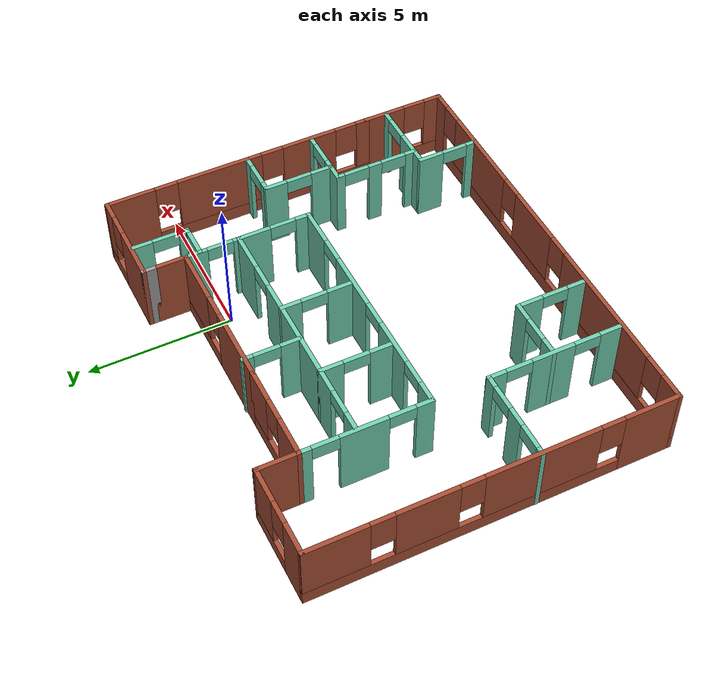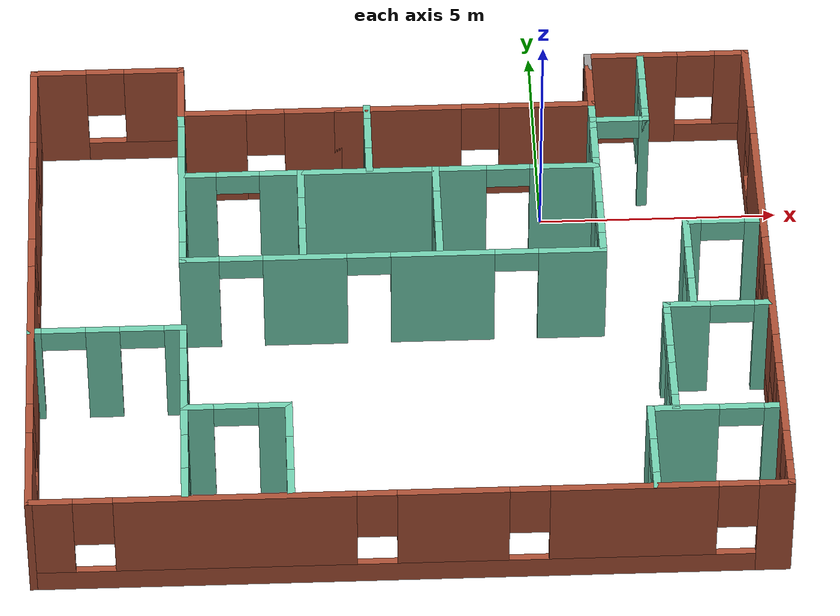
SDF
<?xml version='1.0'?>
<sdf version='1.6'>
  <model name='my_apartment'>
    <pose frame=''>-3.10653 -3.79856 0 0 -0 0</pose>
    <link name='Wall_0'>
      <pose frame=''>1.52918 4.775 0 0 -0 0</pose>
      <visual name='Wall_0_Visual_0'>
        <pose frame=''>-1.4096 0 1.25 0 -0 0</pose>
        <geometry>
          <box>
            <size>2.6808 0.15 2.5</size>
          </box>
        </geometry>
        <material>
          <script>
            <uri>file://media/materials/scripts/gazebo.material</uri>
            <name>Gazebo/Bricks</name>
          </script>
          <ambient>0.435294 0.796078 0.67451 1</ambient>
        </material>
        <meta>
          <layer>0</layer>
        </meta>
      </visual>
      <collision name='Wall_0_Collision_0'>
        <geometry>
          <box>
            <size>2.6808 0.15 2.5</size>
          </box>
        </geometry>
        <pose frame=''>-1.4096 0 1.25 0 -0 0</pose>
      </collision>
      <visual name='Wall_0_Visual_1'>
        <pose frame=''>1.3404 0 0.25 0 -0 0</pose>
        <geometry>
          <box>
            <size>2.8192 0.15 0.5</size>
          </box>
        </geometry>
        <material>
          <script>
            <uri>file://media/materials/scripts/gazebo.material</uri>
            <name>Gazebo/Bricks</name>
          </script>
          <ambient>0.435294 0.796078 0.67451 1</ambient>
        </material>
        <meta>
          <layer>0</layer>
        </meta>
      </visual>
      <collision name='Wall_0_Collision_1'>
        <geometry>
          <box>
            <size>2.8192 0.15 0.5</size>
          </box>
        </geometry>
        <pose frame=''>1.3404 0 0.25 0 -0 0</pose>
      </collision>
      <visual name='Wall_0_Visual_2'>
        <pose frame=''>1.7404 0 1.5 0 -0 0</pose>
        <geometry>
          <box>
            <size>2.0192 0.15 2</size>
          </box>
        </geometry>
        <material>
          <script>
            <uri>file://media/materials/scripts/gazebo.material</uri>
            <name>Gazebo/Bricks</name>
          </script>
          <ambient>0.435294 0.796078 0.67451 1</ambient>
        </material>
        <meta>
          <layer>0</layer>
        </meta>
      </visual>
      <collision name='Wall_0_Collision_2'>
        <geometry>
          <box>
            <size>2.0192 0.15 2</size>
          </box>
        </geometry>
        <pose frame=''>1.7404 0 1.5 0 -0 0</pose>
      </collision>
      <visual name='Wall_0_Visual_3'>
        <pose frame=''>0.330804 0 1.9 0 -0 0</pose>
        <geometry>
          <box>
            <size>0.8 0.15 1.2</size>
          </box>
        </geometry>
        <material>
          <script>
            <uri>file://media/materials/scripts/gazebo.material</uri>
            <name>Gazebo/Bricks</name>
          </script>
          <ambient>0.435294 0.796078 0.67451 1</ambient>
        </material>
        <meta>
          <layer>0</layer>
        </meta>
      </visual>
      <collision name='Wall_0_Collision_3'>
        <geometry>
          <box>
            <size>0.8 0.15 1.2</size>
          </box>
        </geometry>
        <pose frame=''>0.330804 0 1.9 0 -0 0</pose>
      </collision>
    </link>
    <link name='Wall_1'>
      <collision name='Wall_1_Collision'>
        <geometry>
          <box>
            <size>1.25 0.15 2.5</size>
          </box>
        </geometry>
        <pose frame=''>0 0 1.25 0 -0 0</pose>
      </collision>
      <visual name='Wall_1_Visual'>
        <pose frame=''>0 0 1.25 0 -0 0</pose>
        <geometry>
          <box>
            <size>1.25 0.15 2.5</size>
          </box>
        </geometry>
        <material>
          <script>
            <uri>file://media/materials/scripts/gazebo.material</uri>
            <name>Gazebo/Bricks</name>
          </script>
          <ambient>0.435294 0.796078 0.67451 1</ambient>
        </material>
        <meta>
          <layer>0</layer>
        </meta>
      </visual>
      <pose frame=''>4.20418 5.325 0 0 -0 1.5708</pose>
    </link>
    <link name='Wall_10'>
      <pose frame=''>-2.79582 4.775 0 0 -0 0</pose>
      <visual name='Wall_10_Visual_0'>
        <pose frame=''>-1.0014 0 1.25 0 -0 0</pose>
        <geometry>
          <box>
            <size>1.44721 0.15 2.5</size>
          </box>
        </geometry>
        <material>
          <script>
            <uri>file://media/materials/scripts/gazebo.material</uri>
            <name>Gazebo/Bricks</name>
          </script>
          <ambient>0.435294 0.796078 0.67451 1</ambient>
        </material>
        <meta>
          <layer>0</layer>
        </meta>
      </visual>
      <collision name='Wall_10_Collision_0'>
        <geometry>
          <box>
            <size>1.44721 0.15 2.5</size>
          </box>
        </geometry>
        <pose frame=''>-1.0014 0 1.25 0 -0 0</pose>
      </collision>
      <visual name='Wall_10_Visual_1'>
        <pose frame=''>0.723602 0 0.25 0 -0 0</pose>
        <geometry>
          <box>
            <size>2.00279 0.15 0.5</size>
          </box>
        </geometry>
        <material>
          <script>
            <uri>file://media/materials/scripts/gazebo.material</uri>
            <name>Gazebo/Bricks</name>
          </script>
          <ambient>0.435294 0.796078 0.67451 1</ambient>
        </material>
        <meta>
          <layer>0</layer>
        </meta>
      </visual>
      <collision name='Wall_10_Collision_1'>
        <geometry>
          <box>
            <size>2.00279 0.15 0.5</size>
          </box>
        </geometry>
        <pose frame=''>0.723602 0 0.25 0 -0 0</pose>
      </collision>
      <visual name='Wall_10_Visual_2'>
        <pose frame=''>1.1236 0 1.5 0 -0 0</pose>
        <geometry>
          <box>
            <size>1.2028 0.15 2</size>
          </box>
        </geometry>
        <material>
          <script>
            <uri>file://media/materials/scripts/gazebo.material</uri>
            <name>Gazebo/Bricks</name>
          </script>
          <ambient>0.435294 0.796078 0.67451 1</ambient>
        </material>
        <meta>
          <layer>0</layer>
        </meta>
      </visual>
      <collision name='Wall_10_Collision_2'>
        <geometry>
          <box>
            <size>1.2028 0.15 2</size>
          </box>
        </geometry>
        <pose frame=''>1.1236 0 1.5 0 -0 0</pose>
      </collision>
      <visual name='Wall_10_Visual_3'>
        <pose frame=''>0.122205 0 1.9 0 -0 0</pose>
        <geometry>
          <box>
            <size>0.8 0.15 1.2</size>
          </box>
        </geometry>
        <material>
          <script>
            <uri>file://media/materials/scripts/gazebo.material</uri>
            <name>Gazebo/Bricks</name>
          </script>
          <ambient>0.435294 0.796078 0.67451 1</ambient>
        </material>
        <meta>
          <layer>0</layer>
        </meta>
      </visual>
      <collision name='Wall_10_Collision_3'>
        <geometry>
          <box>
            <size>0.8 0.15 1.2</size>
          </box>
        </geometry>
        <pose frame=''>0.122205 0 1.9 0 -0 0</pose>
      </collision>
    </link>
    <link name='Wall_12'>
      <pose frame=''>-4.44565 2.59978 0 0 0 -1.57072</pose>
      <visual name='Wall_12_Visual_0'>
        <pose frame=''>-2.01587 0 1.25 0 -0 0</pose>
        <geometry>
          <box>
            <size>0.468264 0.15 2.5</size>
          </box>
        </geometry>
        <material>
          <script>
            <uri>file://media/materials/scripts/gazebo.material</uri>
            <name>Gazebo/Grey</name>
          </script>
          <ambient>0.435294 0.796078 0.67451 1</ambient>
        </material>
        <meta>
          <layer>0</layer>
        </meta>
      </visual>
      <collision name='Wall_12_Collision_0'>
        <geometry>
          <box>
            <size>0.468264 0.15 2.5</size>
          </box>
        </geometry>
        <pose frame=''>-2.01587 0 1.25 0 -0 0</pose>
      </collision>
      <visual name='Wall_12_Visual_1'>
        <pose frame=''>-0.071119 0 1.25 0 -0 0</pose>
        <geometry>
          <box>
            <size>1.62123 0.15 2.5</size>
          </box>
        </geometry>
        <material>
          <script>
            <uri>file://media/materials/scripts/gazebo.material</uri>
            <name>Gazebo/Grey</name>
          </script>
          <ambient>0.435294 0.796078 0.67451 1</ambient>
        </material>
        <meta>
          <layer>0</layer>
        </meta>
      </visual>
      <collision name='Wall_12_Collision_1'>
        <geometry>
          <box>
            <size>1.62123 0.15 2.5</size>
          </box>
        </geometry>
        <pose frame=''>-0.071119 0 1.25 0 -0 0</pose>
      </collision>
      <visual name='Wall_12_Visual_2'>
        <pose frame=''>1.94475 0 1.25 0 -0 0</pose>
        <geometry>
          <box>
            <size>0.610503 0.15 2.5</size>
          </box>
        </geometry>
        <material>
          <script>
            <uri>file://media/materials/scripts/gazebo.material</uri>
            <name>Gazebo/Grey</name>
          </script>
          <ambient>0.435294 0.796078 0.67451 1</ambient>
        </material>
        <meta>
          <layer>0</layer>
        </meta>
      </visual>
      <collision name='Wall_12_Collision_2'>
        <geometry>
          <box>
            <size>0.610503 0.15 2.5</size>
          </box>
        </geometry>
        <pose frame=''>1.94475 0 1.25 0 -0 0</pose>
      </collision>
      <visual name='Wall_12_Visual_3'>
        <pose frame=''>-1.33174 0 2.25 0 -0 0</pose>
        <geometry>
          <box>
            <size>0.9 0.15 0.5</size>
          </box>
        </geometry>
        <material>
          <script>
            <uri>file://media/materials/scripts/gazebo.material</uri>
            <name>Gazebo/Grey</name>
          </script>
          <ambient>0.435294 0.796078 0.67451 1</ambient>
        </material>
        <meta>
          <layer>0</layer>
        </meta>
      </visual>
      <collision name='Wall_12_Collision_3'>
        <geometry>
          <box>
            <size>0.9 0.15 0.5</size>
          </box>
        </geometry>
        <pose frame=''>-1.33174 0 2.25 0 -0 0</pose>
      </collision>
      <visual name='Wall_12_Visual_4'>
        <pose frame=''>1.1895 0 2.25 0 -0 0</pose>
        <geometry>
          <box>
            <size>0.9 0.15 0.5</size>
          </box>
        </geometry>
        <material>
          <script>
            <uri>file://media/materials/scripts/gazebo.material</uri>
            <name>Gazebo/Grey</name>
          </script>
          <ambient>0.435294 0.796078 0.67451 1</ambient>
        </material>
        <meta>
          <layer>0</layer>
        </meta>
      </visual>
      <collision name='Wall_12_Collision_4'>
        <geometry>
          <box>
            <size>0.9 0.15 0.5</size>
          </box>
        </geometry>
        <pose frame=''>1.1895 0 2.25 0 -0 0</pose>
      </collision>
    </link>
    <link name='Wall_13'>
      <pose frame=''>-0.120473 0.424565 0 0 -0 0</pose>
      <visual name='Wall_13_Visual_0'>
        <pose frame=''>-3.99093 0 1.25 0 -0 0</pose>
        <geometry>
          <box>
            <size>0.818142 0.15 2.5</size>
          </box>
        </geometry>
        <material>
          <script>
            <uri>file://media/materials/scripts/gazebo.material</uri>
            <name>Gazebo/Grey</name>
          </script>
          <ambient>0.435294 0.796078 0.67451 1</ambient>
        </material>
        <meta>
          <layer>0</layer>
        </meta>
      </visual>
      <collision name='Wall_13_Collision_0'>
        <geometry>
          <box>
            <size>0.818142 0.15 2.5</size>
          </box>
        </geometry>
        <pose frame=''>-3.99093 0 1.25 0 -0 0</pose>
      </collision>
      <visual name='Wall_13_Visual_1'>
        <pose frame=''>-1.8163 0 1.25 0 -0 0</pose>
        <geometry>
          <box>
            <size>1.73111 0.15 2.5</size>
          </box>
        </geometry>
        <material>
          <script>
            <uri>file://media/materials/scripts/gazebo.material</uri>
            <name>Gazebo/Grey</name>
          </script>
          <ambient>0.435294 0.796078 0.67451 1</ambient>
        </material>
        <meta>
          <layer>0</layer>
        </meta>
      </visual>
      <collision name='Wall_13_Collision_1'>
        <geometry>
          <box>
            <size>1.73111 0.15 2.5</size>
          </box>
        </geometry>
        <pose frame=''>-1.8163 0 1.25 0 -0 0</pose>
      </collision>
      <visual name='Wall_13_Visual_2'>
        <pose frame=''>1.02013 0 1.25 0 -0 0</pose>
        <geometry>
          <box>
            <size>2.14175 0.15 2.5</size>
          </box>
        </geometry>
        <material>
          <script>
            <uri>file://media/materials/scripts/gazebo.material</uri>
            <name>Gazebo/Grey</name>
          </script>
          <ambient>0.435294 0.796078 0.67451 1</ambient>
        </material>
        <meta>
          <layer>0</layer>
        </meta>
      </visual>
      <collision name='Wall_13_Collision_2'>
        <geometry>
          <box>
            <size>2.14175 0.15 2.5</size>
          </box>
        </geometry>
        <pose frame=''>1.02013 0 1.25 0 -0 0</pose>
      </collision>
      <visual name='Wall_13_Visual_3'>
        <pose frame=''>3.6955 0 1.25 0 -0 0</pose>
        <geometry>
          <box>
            <size>1.40899 0.15 2.5</size>
          </box>
        </geometry>
        <material>
          <script>
            <uri>file://media/materials/scripts/gazebo.material</uri>
            <name>Gazebo/Grey</name>
          </script>
          <ambient>0.435294 0.796078 0.67451 1</ambient>
        </material>
        <meta>
          <layer>0</layer>
        </meta>
      </visual>
      <collision name='Wall_13_Collision_3'>
        <geometry>
          <box>
            <size>1.40899 0.15 2.5</size>
          </box>
        </geometry>
        <pose frame=''>3.6955 0 1.25 0 -0 0</pose>
      </collision>
      <visual name='Wall_13_Visual_4'>
        <pose frame=''>-3.13186 0 2.25 0 -0 0</pose>
        <geometry>
          <box>
            <size>0.9 0.15 0.5</size>
          </box>
        </geometry>
        <material>
          <script>
            <uri>file://media/materials/scripts/gazebo.material</uri>
            <name>Gazebo/Grey</name>
          </script>
          <ambient>0.435294 0.796078 0.67451 1</ambient>
        </material>
        <meta>
          <layer>0</layer>
        </meta>
      </visual>
      <collision name='Wall_13_Collision_4'>
        <geometry>
          <box>
            <size>0.9 0.15 0.5</size>
          </box>
        </geometry>
        <pose frame=''>-3.13186 0 2.25 0 -0 0</pose>
      </collision>
      <visual name='Wall_13_Visual_5'>
        <pose frame=''>-0.500745 0 2.25 0 -0 0</pose>
        <geometry>
          <box>
            <size>0.9 0.15 0.5</size>
          </box>
        </geometry>
        <material>
          <script>
            <uri>file://media/materials/scripts/gazebo.material</uri>
            <name>Gazebo/Grey</name>
          </script>
          <ambient>0.435294 0.796078 0.67451 1</ambient>
        </material>
        <meta>
          <layer>0</layer>
        </meta>
      </visual>
      <collision name='Wall_13_Collision_5'>
        <geometry>
          <box>
            <size>0.9 0.15 0.5</size>
          </box>
        </geometry>
        <pose frame=''>-0.500745 0 2.25 0 -0 0</pose>
      </collision>
      <visual name='Wall_13_Visual_6'>
        <pose frame=''>2.54101 0 2.25 0 -0 0</pose>
        <geometry>
          <box>
            <size>0.9 0.15 0.5</size>
          </box>
        </geometry>
        <material>
          <script>
            <uri>file://media/materials/scripts/gazebo.material</uri>
            <name>Gazebo/Grey</name>
          </script>
          <ambient>0.435294 0.796078 0.67451 1</ambient>
        </material>
        <meta>
          <layer>0</layer>
        </meta>
      </visual>
      <collision name='Wall_13_Collision_6'>
        <geometry>
          <box>
            <size>0.9 0.15 0.5</size>
          </box>
        </geometry>
        <pose frame=''>2.54101 0 2.25 0 -0 0</pose>
      </collision>
    </link>
    <link name='Wall_17'>
      <pose frame=''>4.20435 2.59978 0 0 -0 1.57088</pose>
      <visual name='Wall_17_Visual_0'>
        <pose frame=''>-1.96795 0 1.25 0 -0 0</pose>
        <geometry>
          <box>
            <size>0.564378 0.15 2.5</size>
          </box>
        </geometry>
        <material>
          <script>
            <uri>file://media/materials/scripts/gazebo.material</uri>
            <name>Gazebo/Grey</name>
          </script>
          <ambient>0.435294 0.796078 0.67451 1</ambient>
        </material>
        <meta>
          <layer>0</layer>
        </meta>
      </visual>
      <collision name='Wall_17_Collision_0'>
        <geometry>
          <box>
            <size>0.564378 0.15 2.5</size>
          </box>
        </geometry>
        <pose frame=''>-1.96795 0 1.25 0 -0 0</pose>
      </collision>
      <visual name='Wall_17_Visual_1'>
        <pose frame=''>-0.125495 0 1.25 0 -0 0</pose>
        <geometry>
          <box>
            <size>1.32054 0.15 2.5</size>
          </box>
        </geometry>
        <material>
          <script>
            <uri>file://media/materials/scripts/gazebo.material</uri>
            <name>Gazebo/Grey</name>
          </script>
          <ambient>0.435294 0.796078 0.67451 1</ambient>
        </material>
        <meta>
          <layer>0</layer>
        </meta>
      </visual>
      <collision name='Wall_17_Collision_1'>
        <geometry>
          <box>
            <size>1.32054 0.15 2.5</size>
          </box>
        </geometry>
        <pose frame=''>-0.125495 0 1.25 0 -0 0</pose>
      </collision>
      <visual name='Wall_17_Visual_2'>
        <pose frame=''>1.84246 0 1.25 0 -0 0</pose>
        <geometry>
          <box>
            <size>0.815367 0.15 2.5</size>
          </box>
        </geometry>
        <material>
          <script>
            <uri>file://media/materials/scripts/gazebo.material</uri>
            <name>Gazebo/Grey</name>
          </script>
          <ambient>0.435294 0.796078 0.67451 1</ambient>
        </material>
        <meta>
          <layer>0</layer>
        </meta>
      </visual>
      <collision name='Wall_17_Collision_2'>
        <geometry>
          <box>
            <size>0.815367 0.15 2.5</size>
          </box>
        </geometry>
        <pose frame=''>1.84246 0 1.25 0 -0 0</pose>
      </collision>
      <visual name='Wall_17_Visual_3'>
        <pose frame=''>-1.23577 0 2.25 0 -0 0</pose>
        <geometry>
          <box>
            <size>0.9 0.15 0.5</size>
          </box>
        </geometry>
        <material>
          <script>
            <uri>file://media/materials/scripts/gazebo.material</uri>
            <name>Gazebo/Grey</name>
          </script>
          <ambient>0.435294 0.796078 0.67451 1</ambient>
        </material>
        <meta>
          <layer>0</layer>
        </meta>
      </visual>
      <collision name='Wall_17_Collision_3'>
        <geometry>
          <box>
            <size>0.9 0.15 0.5</size>
          </box>
        </geometry>
        <pose frame=''>-1.23577 0 2.25 0 -0 0</pose>
      </collision>
      <visual name='Wall_17_Visual_4'>
        <pose frame=''>0.984776 0 2.25 0 -0 0</pose>
        <geometry>
          <box>
            <size>0.9 0.15 0.5</size>
          </box>
        </geometry>
        <material>
          <script>
            <uri>file://media/materials/scripts/gazebo.material</uri>
            <name>Gazebo/Grey</name>
          </script>
          <ambient>0.435294 0.796078 0.67451 1</ambient>
        </material>
        <meta>
          <layer>0</layer>
        </meta>
      </visual>
      <collision name='Wall_17_Collision_4'>
        <geometry>
          <box>
            <size>0.9 0.15 0.5</size>
          </box>
        </geometry>
        <pose frame=''>0.984776 0 2.25 0 -0 0</pose>
      </collision>
    </link>
    <link name='Wall_19'>
      <pose frame=''>-0.118146 2.91521 0 0 -0 0</pose>
      <visual name='Wall_19_Visual_0'>
        <pose frame=''>-3.9948 0 1.25 0 -0 0</pose>
        <geometry>
          <box>
            <size>0.760398 0.15 2.5</size>
          </box>
        </geometry>
        <material>
          <script>
            <uri>file://media/materials/scripts/gazebo.material</uri>
            <name>Gazebo/Grey</name>
          </script>
          <ambient>0.435294 0.796078 0.67451 1</ambient>
        </material>
        <meta>
          <layer>0</layer>
        </meta>
      </visual>
      <collision name='Wall_19_Collision_0'>
        <geometry>
          <box>
            <size>0.760398 0.15 2.5</size>
          </box>
        </geometry>
        <pose frame=''>-3.9948 0 1.25 0 -0 0</pose>
      </collision>
      <visual name='Wall_19_Visual_1'>
        <pose frame=''>-0.343379 0 1.25 0 -0 0</pose>
        <geometry>
          <box>
            <size>4.74245 0.15 2.5</size>
          </box>
        </geometry>
        <material>
          <script>
            <uri>file://media/materials/scripts/gazebo.material</uri>
            <name>Gazebo/Grey</name>
          </script>
          <ambient>0.435294 0.796078 0.67451 1</ambient>
        </material>
        <meta>
          <layer>0</layer>
        </meta>
      </visual>
      <collision name='Wall_19_Collision_1'>
        <geometry>
          <box>
            <size>4.74245 0.15 2.5</size>
          </box>
        </geometry>
        <pose frame=''>-0.343379 0 1.25 0 -0 0</pose>
      </collision>
      <visual name='Wall_19_Visual_2'>
        <pose frame=''>3.65142 0 1.25 0 -0 0</pose>
        <geometry>
          <box>
            <size>1.44716 0.15 2.5</size>
          </box>
        </geometry>
        <material>
          <script>
            <uri>file://media/materials/scripts/gazebo.material</uri>
            <name>Gazebo/Grey</name>
          </script>
          <ambient>0.435294 0.796078 0.67451 1</ambient>
        </material>
        <meta>
          <layer>0</layer>
        </meta>
      </visual>
      <collision name='Wall_19_Collision_2'>
        <geometry>
          <box>
            <size>1.44716 0.15 2.5</size>
          </box>
        </geometry>
        <pose frame=''>3.65142 0 1.25 0 -0 0</pose>
      </collision>
      <visual name='Wall_19_Visual_3'>
        <pose frame=''>-3.1646 0 2.25 0 -0 0</pose>
        <geometry>
          <box>
            <size>0.9 0.15 0.5</size>
          </box>
        </geometry>
        <material>
          <script>
            <uri>file://media/materials/scripts/gazebo.material</uri>
            <name>Gazebo/Grey</name>
          </script>
          <ambient>0.435294 0.796078 0.67451 1</ambient>
        </material>
        <meta>
          <layer>0</layer>
        </meta>
      </visual>
      <collision name='Wall_19_Collision_3'>
        <geometry>
          <box>
            <size>0.9 0.15 0.5</size>
          </box>
        </geometry>
        <pose frame=''>-3.1646 0 2.25 0 -0 0</pose>
      </collision>
      <visual name='Wall_19_Visual_4'>
        <pose frame=''>2.47784 0 2.25 0 -0 0</pose>
        <geometry>
          <box>
            <size>0.9 0.15 0.5</size>
          </box>
        </geometry>
        <material>
          <script>
            <uri>file://media/materials/scripts/gazebo.material</uri>
            <name>Gazebo/Grey</name>
          </script>
          <ambient>0.435294 0.796078 0.67451 1</ambient>
        </material>
        <meta>
          <layer>0</layer>
        </meta>
      </visual>
      <collision name='Wall_19_Collision_4'>
        <geometry>
          <box>
            <size>0.9 0.15 0.5</size>
          </box>
        </geometry>
        <pose frame=''>2.47784 0 2.25 0 -0 0</pose>
      </collision>
    </link>
    <link name='Wall_2'>
      <collision name='Wall_2_Collision'>
        <geometry>
          <box>
            <size>0.5 0.15 2.5</size>
          </box>
        </geometry>
        <pose frame=''>0 0 1.25 0 -0 0</pose>
      </collision>
      <visual name='Wall_2_Visual'>
        <pose frame=''>0 0 1.25 0 -0 0</pose>
        <geometry>
          <box>
            <size>0.5 0.15 2.5</size>
          </box>
        </geometry>
        <material>
          <script>
            <uri>file://media/materials/scripts/gazebo.material</uri>
            <name>Gazebo/Grey</name>
          </script>
          <ambient>1 1 1 1</ambient>
        </material>
        <meta>
          <layer>0</layer>
        </meta>
      </visual>
      <pose frame=''>4.20418 6.05 0 0 -0 1.5708</pose>
    </link>
    <link name='Wall_21'>
      <pose frame=''>-1.97093 1.74021 0 0 0 -1.5708</pose>
      <visual name='Wall_21_Visual_0'>
        <pose frame=''>-0.835388 0 1.25 0 -0 0</pose>
        <geometry>
          <box>
            <size>0.829225 0.15 2.5</size>
          </box>
        </geometry>
        <material>
          <script>
            <uri>file://media/materials/scripts/gazebo.material</uri>
            <name>Gazebo/Grey</name>
          </script>
          <ambient>0.435294 0.796078 0.67451 1</ambient>
        </material>
        <meta>
          <layer>0</layer>
        </meta>
      </visual>
      <collision name='Wall_21_Collision_0'>
        <geometry>
          <box>
            <size>0.829225 0.15 2.5</size>
          </box>
        </geometry>
        <pose frame=''>-0.835388 0 1.25 0 -0 0</pose>
      </collision>
      <visual name='Wall_21_Visual_1'>
        <pose frame=''>0.864612 0 1.25 0 -0 0</pose>
        <geometry>
          <box>
            <size>0.770775 0.15 2.5</size>
          </box>
        </geometry>
        <material>
          <script>
            <uri>file://media/materials/scripts/gazebo.material</uri>
            <name>Gazebo/Grey</name>
          </script>
          <ambient>0.435294 0.796078 0.67451 1</ambient>
        </material>
        <meta>
          <layer>0</layer>
        </meta>
      </visual>
      <collision name='Wall_21_Collision_1'>
        <geometry>
          <box>
            <size>0.770775 0.15 2.5</size>
          </box>
        </geometry>
        <pose frame=''>0.864612 0 1.25 0 -0 0</pose>
      </collision>
      <visual name='Wall_21_Visual_2'>
        <pose frame=''>0.029225 0 2.25 0 -0 0</pose>
        <geometry>
          <box>
            <size>0.9 0.15 0.5</size>
          </box>
        </geometry>
        <material>
          <script>
            <uri>file://media/materials/scripts/gazebo.material</uri>
            <name>Gazebo/Grey</name>
          </script>
          <ambient>0.435294 0.796078 0.67451 1</ambient>
        </material>
        <meta>
          <layer>0</layer>
        </meta>
      </visual>
      <collision name='Wall_21_Collision_2'>
        <geometry>
          <box>
            <size>0.9 0.15 0.5</size>
          </box>
        </geometry>
        <pose frame=''>0.029225 0 2.25 0 -0 0</pose>
      </collision>
    </link>
    <link name='Wall_23'>
      <pose frame=''>0.843373 1.74021 0 0 0 -1.5708</pose>
      <visual name='Wall_23_Visual_0'>
        <pose frame=''>-0.881649 0 1.25 0 -0 0</pose>
        <geometry>
          <box>
            <size>0.736702 0.15 2.5</size>
          </box>
        </geometry>
        <material>
          <script>
            <uri>file://media/materials/scripts/gazebo.material</uri>
            <name>Gazebo/Grey</name>
          </script>
          <ambient>0.435294 0.796078 0.67451 1</ambient>
        </material>
        <meta>
          <layer>0</layer>
        </meta>
      </visual>
      <collision name='Wall_23_Collision_0'>
        <geometry>
          <box>
            <size>0.736702 0.15 2.5</size>
          </box>
        </geometry>
        <pose frame=''>-0.881649 0 1.25 0 -0 0</pose>
      </collision>
      <visual name='Wall_23_Visual_1'>
        <pose frame=''>0.818351 0 1.25 0 -0 0</pose>
        <geometry>
          <box>
            <size>0.863298 0.15 2.5</size>
          </box>
        </geometry>
        <material>
          <script>
            <uri>file://media/materials/scripts/gazebo.material</uri>
            <name>Gazebo/Grey</name>
          </script>
          <ambient>0.435294 0.796078 0.67451 1</ambient>
        </material>
        <meta>
          <layer>0</layer>
        </meta>
      </visual>
      <collision name='Wall_23_Collision_1'>
        <geometry>
          <box>
            <size>0.863298 0.15 2.5</size>
          </box>
        </geometry>
        <pose frame=''>0.818351 0 1.25 0 -0 0</pose>
      </collision>
      <visual name='Wall_23_Visual_2'>
        <pose frame=''>-0.063298 0 2.25 0 -0 0</pose>
        <geometry>
          <box>
            <size>0.9 0.15 0.5</size>
          </box>
        </geometry>
        <material>
          <script>
            <uri>file://media/materials/scripts/gazebo.material</uri>
            <name>Gazebo/Grey</name>
          </script>
          <ambient>0.435294 0.796078 0.67451 1</ambient>
        </material>
        <meta>
          <layer>0</layer>
        </meta>
      </visual>
      <collision name='Wall_23_Collision_2'>
        <geometry>
          <box>
            <size>0.9 0.15 0.5</size>
          </box>
        </geometry>
        <pose frame=''>-0.063298 0 2.25 0 -0 0</pose>
      </collision>
    </link>
    <link name='Wall_25'>
      <pose frame=''>-0.533187 3.90139 0 0 -0 1.5708</pose>
      <visual name='Wall_25_Visual_0'>
        <pose frame=''>-0.652107 0 1.25 0 -0 0</pose>
        <geometry>
          <box>
            <size>0.695786 0.15 2.5</size>
          </box>
        </geometry>
        <material>
          <script>
            <uri>file://media/materials/scripts/gazebo.material</uri>
            <name>Gazebo/Grey</name>
          </script>
          <ambient>0.435294 0.796078 0.67451 1</ambient>
        </material>
        <meta>
          <layer>0</layer>
        </meta>
      </visual>
      <collision name='Wall_25_Collision_0'>
        <geometry>
          <box>
            <size>0.695786 0.15 2.5</size>
          </box>
        </geometry>
        <pose frame=''>-0.652107 0 1.25 0 -0 0</pose>
      </collision>
      <visual name='Wall_25_Visual_1'>
        <pose frame=''>0.797893 0 1.25 0 -0 0</pose>
        <geometry>
          <box>
            <size>0.404214 0.15 2.5</size>
          </box>
        </geometry>
        <material>
          <script>
            <uri>file://media/materials/scripts/gazebo.material</uri>
            <name>Gazebo/Grey</name>
          </script>
          <ambient>0.435294 0.796078 0.67451 1</ambient>
        </material>
        <meta>
          <layer>0</layer>
        </meta>
      </visual>
      <collision name='Wall_25_Collision_1'>
        <geometry>
          <box>
            <size>0.404214 0.15 2.5</size>
          </box>
        </geometry>
        <pose frame=''>0.797893 0 1.25 0 -0 0</pose>
      </collision>
      <visual name='Wall_25_Visual_2'>
        <pose frame=''>0.145786 0 2.25 0 -0 0</pose>
        <geometry>
          <box>
            <size>0.9 0.15 0.5</size>
          </box>
        </geometry>
        <material>
          <script>
            <uri>file://media/materials/scripts/gazebo.material</uri>
            <name>Gazebo/Grey</name>
          </script>
          <ambient>0.435294 0.796078 0.67451 1</ambient>
        </material>
        <meta>
          <layer>0</layer>
        </meta>
      </visual>
      <collision name='Wall_25_Collision_2'>
        <geometry>
          <box>
            <size>0.9 0.15 0.5</size>
          </box>
        </geometry>
        <pose frame=''>0.145786 0 2.25 0 -0 0</pose>
      </collision>
    </link>
    <link name='Wall_27'>
      <pose frame=''>4.7693 4.27848 0 0 -0 0</pose>
      <visual name='Wall_27_Visual_0'>
        <pose frame=''>-0.558063 0 1.25 0 -0 0</pose>
        <geometry>
          <box>
            <size>0.133873 0.15 2.5</size>
          </box>
        </geometry>
        <material>
          <script>
            <uri>file://media/materials/scripts/gazebo.material</uri>
            <name>Gazebo/Grey</name>
          </script>
          <ambient>0.435294 0.796078 0.67451 1</ambient>
        </material>
        <meta>
          <layer>0</layer>
        </meta>
      </visual>
      <collision name='Wall_27_Collision_0'>
        <geometry>
          <box>
            <size>0.133873 0.15 2.5</size>
          </box>
        </geometry>
        <pose frame=''>-0.558063 0 1.25 0 -0 0</pose>
      </collision>
      <visual name='Wall_27_Visual_1'>
        <pose frame=''>0.516937 0 1.25 0 -0 0</pose>
        <geometry>
          <box>
            <size>0.216127 0.15 2.5</size>
          </box>
        </geometry>
        <material>
          <script>
            <uri>file://media/materials/scripts/gazebo.material</uri>
            <name>Gazebo/Grey</name>
          </script>
          <ambient>0.435294 0.796078 0.67451 1</ambient>
        </material>
        <meta>
          <layer>0</layer>
        </meta>
      </visual>
      <collision name='Wall_27_Collision_1'>
        <geometry>
          <box>
            <size>0.216127 0.15 2.5</size>
          </box>
        </geometry>
        <pose frame=''>0.516937 0 1.25 0 -0 0</pose>
      </collision>
      <visual name='Wall_27_Visual_2'>
        <pose frame=''>-0.041127 0 2.25 0 -0 0</pose>
        <geometry>
          <box>
            <size>0.9 0.15 0.5</size>
          </box>
        </geometry>
        <material>
          <script>
            <uri>file://media/materials/scripts/gazebo.material</uri>
            <name>Gazebo/Grey</name>
          </script>
          <ambient>0.435294 0.796078 0.67451 1</ambient>
        </material>
        <meta>
          <layer>0</layer>
        </meta>
      </visual>
      <collision name='Wall_27_Collision_2'>
        <geometry>
          <box>
            <size>0.9 0.15 0.5</size>
          </box>
        </geometry>
        <pose frame=''>-0.041127 0 2.25 0 -0 0</pose>
      </collision>
    </link>
    <link name='Wall_28'>
      <pose frame=''>5.3193 5.20348 0 0 -0 1.5708</pose>
      <visual name='Wall_28_Visual_0'>
        <pose frame=''>-0.805845 0 1.25 0 -0 0</pose>
        <geometry>
          <box>
            <size>0.38831 0.15 2.5</size>
          </box>
        </geometry>
        <material>
          <script>
            <uri>file://media/materials/scripts/gazebo.material</uri>
            <name>Gazebo/Grey</name>
          </script>
          <ambient>0.435294 0.796078 0.67451 1</ambient>
        </material>
        <meta>
          <layer>0</layer>
        </meta>
      </visual>
      <collision name='Wall_28_Collision_0'>
        <geometry>
          <box>
            <size>0.38831 0.15 2.5</size>
          </box>
        </geometry>
        <pose frame=''>-0.805845 0 1.25 0 -0 0</pose>
      </collision>
      <visual name='Wall_28_Visual_1'>
        <pose frame=''>0.644155 0 1.25 0 -0 0</pose>
        <geometry>
          <box>
            <size>0.71169 0.15 2.5</size>
          </box>
        </geometry>
        <material>
          <script>
            <uri>file://media/materials/scripts/gazebo.material</uri>
            <name>Gazebo/Grey</name>
          </script>
          <ambient>0.435294 0.796078 0.67451 1</ambient>
        </material>
        <meta>
          <layer>0</layer>
        </meta>
      </visual>
      <collision name='Wall_28_Collision_1'>
        <geometry>
          <box>
            <size>0.71169 0.15 2.5</size>
          </box>
        </geometry>
        <pose frame=''>0.644155 0 1.25 0 -0 0</pose>
      </collision>
      <visual name='Wall_28_Visual_2'>
        <pose frame=''>-0.16169 0 2.25 0 -0 0</pose>
        <geometry>
          <box>
            <size>0.9 0.15 0.5</size>
          </box>
        </geometry>
        <material>
          <script>
            <uri>file://media/materials/scripts/gazebo.material</uri>
            <name>Gazebo/Grey</name>
          </script>
          <ambient>0.435294 0.796078 0.67451 1</ambient>
        </material>
        <meta>
          <layer>0</layer>
        </meta>
      </visual>
      <collision name='Wall_28_Collision_2'>
        <geometry>
          <box>
            <size>0.9 0.15 0.5</size>
          </box>
        </geometry>
        <pose frame=''>-0.16169 0 2.25 0 -0 0</pose>
      </collision>
    </link>
    <link name='Wall_3'>
      <pose frame=''>5.87918 6.225 0 0 -0 0</pose>
      <visual name='Wall_3_Visual_0'>
        <pose frame=''>-0.759972 0 1.25 0 -0 0</pose>
        <geometry>
          <box>
            <size>1.98006 0.15 2.5</size>
          </box>
        </geometry>
        <material>
          <script>
            <uri>file://media/materials/scripts/gazebo.material</uri>
            <name>Gazebo/Bricks</name>
          </script>
          <ambient>0.435294 0.796078 0.67451 1</ambient>
        </material>
        <meta>
          <layer>0</layer>
        </meta>
      </visual>
      <collision name='Wall_3_Collision_0'>
        <geometry>
          <box>
            <size>1.98006 0.15 2.5</size>
          </box>
        </geometry>
        <pose frame=''>-0.759972 0 1.25 0 -0 0</pose>
      </collision>
      <visual name='Wall_3_Visual_1'>
        <pose frame=''>0.990028 0 0.25 0 -0 0</pose>
        <geometry>
          <box>
            <size>1.51994 0.15 0.5</size>
          </box>
        </geometry>
        <material>
          <script>
            <uri>file://media/materials/scripts/gazebo.material</uri>
            <name>Gazebo/Bricks</name>
          </script>
          <ambient>0.435294 0.796078 0.67451 1</ambient>
        </material>
        <meta>
          <layer>0</layer>
        </meta>
      </visual>
      <collision name='Wall_3_Collision_1'>
        <geometry>
          <box>
            <size>1.51994 0.15 0.5</size>
          </box>
        </geometry>
        <pose frame=''>0.990028 0 0.25 0 -0 0</pose>
      </collision>
      <visual name='Wall_3_Visual_2'>
        <pose frame=''>1.39003 0 1.5 0 -0 0</pose>
        <geometry>
          <box>
            <size>0.719944 0.15 2</size>
          </box>
        </geometry>
        <material>
          <script>
            <uri>file://media/materials/scripts/gazebo.material</uri>
            <name>Gazebo/Bricks</name>
          </script>
          <ambient>0.435294 0.796078 0.67451 1</ambient>
        </material>
        <meta>
          <layer>0</layer>
        </meta>
      </visual>
      <collision name='Wall_3_Collision_2'>
        <geometry>
          <box>
            <size>0.719944 0.15 2</size>
          </box>
        </geometry>
        <pose frame=''>1.39003 0 1.5 0 -0 0</pose>
      </collision>
      <visual name='Wall_3_Visual_3'>
        <pose frame=''>0.630056 0 1.9 0 -0 0</pose>
        <geometry>
          <box>
            <size>0.8 0.15 1.2</size>
          </box>
        </geometry>
        <material>
          <script>
            <uri>file://media/materials/scripts/gazebo.material</uri>
            <name>Gazebo/Bricks</name>
          </script>
          <ambient>0.435294 0.796078 0.67451 1</ambient>
        </material>
        <meta>
          <layer>0</layer>
        </meta>
      </visual>
      <collision name='Wall_3_Collision_3'>
        <geometry>
          <box>
            <size>0.8 0.15 1.2</size>
          </box>
        </geometry>
        <pose frame=''>0.630056 0 1.9 0 -0 0</pose>
      </collision>
    </link>
    <link name='Wall_30'>
      <pose frame=''>4.89009 -5.17282 0 0 -0 1.5708</pose>
      <visual name='Wall_30_Visual_0'>
        <pose frame=''>-0.907714 0 1.25 0 -0 0</pose>
        <geometry>
          <box>
            <size>0.434571 0.15 2.5</size>
          </box>
        </geometry>
        <material>
          <script>
            <uri>file://media/materials/scripts/gazebo.material</uri>
            <name>Gazebo/Grey</name>
          </script>
          <ambient>0.435294 0.796078 0.67451 1</ambient>
        </material>
        <meta>
          <layer>0</layer>
        </meta>
      </visual>
      <collision name='Wall_30_Collision_0'>
        <geometry>
          <box>
            <size>0.434571 0.15 2.5</size>
          </box>
        </geometry>
        <pose frame=''>-0.907714 0 1.25 0 -0 0</pose>
      </collision>
      <visual name='Wall_30_Visual_1'>
        <pose frame=''>0.667286 0 1.25 0 -0 0</pose>
        <geometry>
          <box>
            <size>0.915429 0.15 2.5</size>
          </box>
        </geometry>
        <material>
          <script>
            <uri>file://media/materials/scripts/gazebo.material</uri>
            <name>Gazebo/Grey</name>
          </script>
          <ambient>0.435294 0.796078 0.67451 1</ambient>
        </material>
        <meta>
          <layer>0</layer>
        </meta>
      </visual>
      <collision name='Wall_30_Collision_1'>
        <geometry>
          <box>
            <size>0.915429 0.15 2.5</size>
          </box>
        </geometry>
        <pose frame=''>0.667286 0 1.25 0 -0 0</pose>
      </collision>
      <visual name='Wall_30_Visual_2'>
        <pose frame=''>-0.240429 0 2.25 0 -0 0</pose>
        <geometry>
          <box>
            <size>0.9 0.15 0.5</size>
          </box>
        </geometry>
        <material>
          <script>
            <uri>file://media/materials/scripts/gazebo.material</uri>
            <name>Gazebo/Grey</name>
          </script>
          <ambient>0.435294 0.796078 0.67451 1</ambient>
        </material>
        <meta>
          <layer>0</layer>
        </meta>
      </visual>
      <collision name='Wall_30_Collision_2'>
        <geometry>
          <box>
            <size>0.9 0.15 0.5</size>
          </box>
        </geometry>
        <pose frame=''>-0.240429 0 2.25 0 -0 0</pose>
      </collision>
    </link>
    <link name='Wall_31'>
      <pose frame=''>6.19009 -4.12282 0 0 -0 0</pose>
      <visual name='Wall_31_Visual_0'>
        <pose frame=''>-0.648841 0 1.25 0 -0 0</pose>
        <geometry>
          <box>
            <size>1.45232 0.15 2.5</size>
          </box>
        </geometry>
        <material>
          <script>
            <uri>file://media/materials/scripts/gazebo.material</uri>
            <name>Gazebo/Grey</name>
          </script>
          <ambient>0.435294 0.796078 0.67451 1</ambient>
        </material>
        <meta>
          <layer>0</layer>
        </meta>
      </visual>
      <collision name='Wall_31_Collision_0'>
        <geometry>
          <box>
            <size>1.45232 0.15 2.5</size>
          </box>
        </geometry>
        <pose frame=''>-0.648841 0 1.25 0 -0 0</pose>
      </collision>
      <visual name='Wall_31_Visual_1'>
        <pose frame=''>1.17616 0 1.25 0 -0 0</pose>
        <geometry>
          <box>
            <size>0.397682 0.15 2.5</size>
          </box>
        </geometry>
        <material>
          <script>
            <uri>file://media/materials/scripts/gazebo.material</uri>
            <name>Gazebo/Grey</name>
          </script>
          <ambient>0.435294 0.796078 0.67451 1</ambient>
        </material>
        <meta>
          <layer>0</layer>
        </meta>
      </visual>
      <collision name='Wall_31_Collision_1'>
        <geometry>
          <box>
            <size>0.397682 0.15 2.5</size>
          </box>
        </geometry>
        <pose frame=''>1.17616 0 1.25 0 -0 0</pose>
      </collision>
      <visual name='Wall_31_Visual_2'>
        <pose frame=''>0.527318 0 2.25 0 -0 0</pose>
        <geometry>
          <box>
            <size>0.9 0.15 0.5</size>
          </box>
        </geometry>
        <material>
          <script>
            <uri>file://media/materials/scripts/gazebo.material</uri>
            <name>Gazebo/Grey</name>
          </script>
          <ambient>0.435294 0.796078 0.67451 1</ambient>
        </material>
        <meta>
          <layer>0</layer>
        </meta>
      </visual>
      <collision name='Wall_31_Collision_2'>
        <geometry>
          <box>
            <size>0.9 0.15 0.5</size>
          </box>
        </geometry>
        <pose frame=''>0.527318 0 2.25 0 -0 0</pose>
      </collision>
    </link>
    <link name='Wall_33'>
      <pose frame=''>5.39896 -2.64667 0 0 -0 1.5708</pose>
      <visual name='Wall_33_Visual_0'>
        <pose frame=''>-1.30584 0 1.25 0 -0 0</pose>
        <geometry>
          <box>
            <size>0.38831 0.15 2.5</size>
          </box>
        </geometry>
        <material>
          <script>
            <uri>file://media/materials/scripts/gazebo.material</uri>
            <name>Gazebo/Grey</name>
          </script>
          <ambient>0.435294 0.796078 0.67451 1</ambient>
        </material>
        <meta>
          <layer>0</layer>
        </meta>
      </visual>
      <collision name='Wall_33_Collision_0'>
        <geometry>
          <box>
            <size>0.38831 0.15 2.5</size>
          </box>
        </geometry>
        <pose frame=''>-1.30584 0 1.25 0 -0 0</pose>
      </collision>
      <visual name='Wall_33_Visual_1'>
        <pose frame=''>0.032228 0 1.25 0 -0 0</pose>
        <geometry>
          <box>
            <size>0.487836 0.15 2.5</size>
          </box>
        </geometry>
        <material>
          <script>
            <uri>file://media/materials/scripts/gazebo.material</uri>
            <name>Gazebo/Grey</name>
          </script>
          <ambient>0.435294 0.796078 0.67451 1</ambient>
        </material>
        <meta>
          <layer>0</layer>
        </meta>
      </visual>
      <collision name='Wall_33_Collision_1'>
        <geometry>
          <box>
            <size>0.487836 0.15 2.5</size>
          </box>
        </geometry>
        <pose frame=''>0.032228 0 1.25 0 -0 0</pose>
      </collision>
      <visual name='Wall_33_Visual_2'>
        <pose frame=''>1.33807 0 1.25 0 -0 0</pose>
        <geometry>
          <box>
            <size>0.323854 0.15 2.5</size>
          </box>
        </geometry>
        <material>
          <script>
            <uri>file://media/materials/scripts/gazebo.material</uri>
            <name>Gazebo/Grey</name>
          </script>
          <ambient>0.435294 0.796078 0.67451 1</ambient>
        </material>
        <meta>
          <layer>0</layer>
        </meta>
      </visual>
      <collision name='Wall_33_Collision_2'>
        <geometry>
          <box>
            <size>0.323854 0.15 2.5</size>
          </box>
        </geometry>
        <pose frame=''>1.33807 0 1.25 0 -0 0</pose>
      </collision>
      <visual name='Wall_33_Visual_3'>
        <pose frame=''>-0.66169 0 2.25 0 -0 0</pose>
        <geometry>
          <box>
            <size>0.9 0.15 0.5</size>
          </box>
        </geometry>
        <material>
          <script>
            <uri>file://media/materials/scripts/gazebo.material</uri>
            <name>Gazebo/Grey</name>
          </script>
          <ambient>0.435294 0.796078 0.67451 1</ambient>
        </material>
        <meta>
          <layer>0</layer>
        </meta>
      </visual>
      <collision name='Wall_33_Collision_3'>
        <geometry>
          <box>
            <size>0.9 0.15 0.5</size>
          </box>
        </geometry>
        <pose frame=''>-0.66169 0 2.25 0 -0 0</pose>
      </collision>
      <visual name='Wall_33_Visual_4'>
        <pose frame=''>0.726146 0 2.25 0 -0 0</pose>
        <geometry>
          <box>
            <size>0.9 0.15 0.5</size>
          </box>
        </geometry>
        <material>
          <script>
            <uri>file://media/materials/scripts/gazebo.material</uri>
            <name>Gazebo/Grey</name>
          </script>
          <ambient>0.435294 0.796078 0.67451 1</ambient>
        </material>
        <meta>
          <layer>0</layer>
        </meta>
      </visual>
      <collision name='Wall_33_Collision_4'>
        <geometry>
          <box>
            <size>0.9 0.15 0.5</size>
          </box>
        </geometry>
        <pose frame=''>0.726146 0 2.25 0 -0 0</pose>
      </collision>
    </link>
    <link name='Wall_34'>
      <pose frame=''>6.44896 -1.22167 0 0 -0 0</pose>
      <visual name='Wall_34_Visual_0'>
        <pose frame=''>-0.641712 0 1.25 0 -0 0</pose>
        <geometry>
          <box>
            <size>0.966575 0.15 2.5</size>
          </box>
        </geometry>
        <material>
          <script>
            <uri>file://media/materials/scripts/gazebo.material</uri>
            <name>Gazebo/Grey</name>
          </script>
          <ambient>0.435294 0.796078 0.67451 1</ambient>
        </material>
        <meta>
          <layer>0</layer>
        </meta>
      </visual>
      <collision name='Wall_34_Collision_0'>
        <geometry>
          <box>
            <size>0.966575 0.15 2.5</size>
          </box>
        </geometry>
        <pose frame=''>-0.641712 0 1.25 0 -0 0</pose>
      </collision>
      <visual name='Wall_34_Visual_1'>
        <pose frame=''>0.933288 0 1.25 0 -0 0</pose>
        <geometry>
          <box>
            <size>0.383425 0.15 2.5</size>
          </box>
        </geometry>
        <material>
          <script>
            <uri>file://media/materials/scripts/gazebo.material</uri>
            <name>Gazebo/Grey</name>
          </script>
          <ambient>0.435294 0.796078 0.67451 1</ambient>
        </material>
        <meta>
          <layer>0</layer>
        </meta>
      </visual>
      <collision name='Wall_34_Collision_1'>
        <geometry>
          <box>
            <size>0.383425 0.15 2.5</size>
          </box>
        </geometry>
        <pose frame=''>0.933288 0 1.25 0 -0 0</pose>
      </collision>
      <visual name='Wall_34_Visual_2'>
        <pose frame=''>0.291575 0 2.25 0 -0 0</pose>
        <geometry>
          <box>
            <size>0.9 0.15 0.5</size>
          </box>
        </geometry>
        <material>
          <script>
            <uri>file://media/materials/scripts/gazebo.material</uri>
            <name>Gazebo/Grey</name>
          </script>
          <ambient>0.435294 0.796078 0.67451 1</ambient>
        </material>
        <meta>
          <layer>0</layer>
        </meta>
      </visual>
      <collision name='Wall_34_Collision_2'>
        <geometry>
          <box>
            <size>0.9 0.15 0.5</size>
          </box>
        </geometry>
        <pose frame=''>0.291575 0 2.25 0 -0 0</pose>
      </collision>
    </link>
    <link name='Wall_36'>
      <pose frame=''>5.9541 -0.005345 0 0 -0 1.5708</pose>
      <visual name='Wall_36_Visual_0'>
        <pose frame=''>-0.859235 0 1.25 0 -0 0</pose>
        <geometry>
          <box>
            <size>0.78153 0.15 2.5</size>
          </box>
        </geometry>
        <material>
          <script>
            <uri>file://media/materials/scripts/gazebo.material</uri>
            <name>Gazebo/Grey</name>
          </script>
          <ambient>0.435294 0.796078 0.67451 1</ambient>
        </material>
        <meta>
          <layer>0</layer>
        </meta>
      </visual>
      <collision name='Wall_36_Collision_0'>
        <geometry>
          <box>
            <size>0.78153 0.15 2.5</size>
          </box>
        </geometry>
        <pose frame=''>-0.859235 0 1.25 0 -0 0</pose>
      </collision>
      <visual name='Wall_36_Visual_1'>
        <pose frame=''>0.840765 0 1.25 0 -0 0</pose>
        <geometry>
          <box>
            <size>0.81847 0.15 2.5</size>
          </box>
        </geometry>
        <material>
          <script>
            <uri>file://media/materials/scripts/gazebo.material</uri>
            <name>Gazebo/Grey</name>
          </script>
          <ambient>0.435294 0.796078 0.67451 1</ambient>
        </material>
        <meta>
          <layer>0</layer>
        </meta>
      </visual>
      <collision name='Wall_36_Collision_1'>
        <geometry>
          <box>
            <size>0.81847 0.15 2.5</size>
          </box>
        </geometry>
        <pose frame=''>0.840765 0 1.25 0 -0 0</pose>
      </collision>
      <visual name='Wall_36_Visual_2'>
        <pose frame=''>-0.01847 0 2.25 0 -0 0</pose>
        <geometry>
          <box>
            <size>0.9 0.15 0.5</size>
          </box>
        </geometry>
        <material>
          <script>
            <uri>file://media/materials/scripts/gazebo.material</uri>
            <name>Gazebo/Grey</name>
          </script>
          <ambient>0.435294 0.796078 0.67451 1</ambient>
        </material>
        <meta>
          <layer>0</layer>
        </meta>
      </visual>
      <collision name='Wall_36_Collision_2'>
        <geometry>
          <box>
            <size>0.9 0.15 0.5</size>
          </box>
        </geometry>
        <pose frame=''>-0.01847 0 2.25 0 -0 0</pose>
      </collision>
    </link>
    <link name='Wall_37'>
      <pose frame=''>6.7541 1.16965 0 0 -0 0</pose>
      <visual name='Wall_37_Visual_0'>
        <pose frame=''>-0.680845 0 1.25 0 -0 0</pose>
        <geometry>
          <box>
            <size>0.38831 0.15 2.5</size>
          </box>
        </geometry>
        <material>
          <script>
            <uri>file://media/materials/scripts/gazebo.material</uri>
            <name>Gazebo/Grey</name>
          </script>
          <ambient>0.435294 0.796078 0.67451 1</ambient>
        </material>
        <meta>
          <layer>0</layer>
        </meta>
      </visual>
      <collision name='Wall_37_Collision_0'>
        <geometry>
          <box>
            <size>0.38831 0.15 2.5</size>
          </box>
        </geometry>
        <pose frame=''>-0.680845 0 1.25 0 -0 0</pose>
      </collision>
      <visual name='Wall_37_Visual_1'>
        <pose frame=''>0.644155 0 1.25 0 -0 0</pose>
        <geometry>
          <box>
            <size>0.46169 0.15 2.5</size>
          </box>
        </geometry>
        <material>
          <script>
            <uri>file://media/materials/scripts/gazebo.material</uri>
            <name>Gazebo/Grey</name>
          </script>
          <ambient>0.435294 0.796078 0.67451 1</ambient>
        </material>
        <meta>
          <layer>0</layer>
        </meta>
      </visual>
      <collision name='Wall_37_Collision_1'>
        <geometry>
          <box>
            <size>0.46169 0.15 2.5</size>
          </box>
        </geometry>
        <pose frame=''>0.644155 0 1.25 0 -0 0</pose>
      </collision>
      <visual name='Wall_37_Visual_2'>
        <pose frame=''>-0.03669 0 2.25 0 -0 0</pose>
        <geometry>
          <box>
            <size>0.9 0.15 0.5</size>
          </box>
        </geometry>
        <material>
          <script>
            <uri>file://media/materials/scripts/gazebo.material</uri>
            <name>Gazebo/Grey</name>
          </script>
          <ambient>0.435294 0.796078 0.67451 1</ambient>
        </material>
        <meta>
          <layer>0</layer>
        </meta>
      </visual>
      <collision name='Wall_37_Collision_2'>
        <geometry>
          <box>
            <size>0.9 0.15 0.5</size>
          </box>
        </geometry>
        <pose frame=''>-0.03669 0 2.25 0 -0 0</pose>
      </collision>
    </link>
    <link name='Wall_4'>
      <pose frame=''>7.55418 1.425 0 0 0 -1.5708</pose>
      <visual name='Wall_4_Visual_0'>
        <pose frame=''>-3.99485 0 1.25 0 -0 0</pose>
        <geometry>
          <box>
            <size>1.76031 0.15 2.5</size>
          </box>
        </geometry>
        <material>
          <script>
            <uri>file://media/materials/scripts/gazebo.material</uri>
            <name>Gazebo/Bricks</name>
          </script>
          <ambient>0.435294 0.796078 0.67451 1</ambient>
        </material>
        <meta>
          <layer>0</layer>
        </meta>
      </visual>
      <collision name='Wall_4_Collision_0'>
        <geometry>
          <box>
            <size>1.76031 0.15 2.5</size>
          </box>
        </geometry>
        <pose frame=''>-3.99485 0 1.25 0 -0 0</pose>
      </collision>
      <visual name='Wall_4_Visual_1'>
        <pose frame=''>0.880153 0 0.25 0 -0 0</pose>
        <geometry>
          <box>
            <size>7.98969 0.15 0.5</size>
          </box>
        </geometry>
        <material>
          <script>
            <uri>file://media/materials/scripts/gazebo.material</uri>
            <name>Gazebo/Bricks</name>
          </script>
          <ambient>0.435294 0.796078 0.67451 1</ambient>
        </material>
        <meta>
          <layer>0</layer>
        </meta>
      </visual>
      <collision name='Wall_4_Collision_1'>
        <geometry>
          <box>
            <size>7.98969 0.15 0.5</size>
          </box>
        </geometry>
        <pose frame=''>0.880153 0 0.25 0 -0 0</pose>
      </collision>
      <visual name='Wall_4_Visual_2'>
        <pose frame=''>-0.771723 0 1.5 0 -0 0</pose>
        <geometry>
          <box>
            <size>3.08594 0.15 2</size>
          </box>
        </geometry>
        <material>
          <script>
            <uri>file://media/materials/scripts/gazebo.material</uri>
            <name>Gazebo/Bricks</name>
          </script>
          <ambient>0.435294 0.796078 0.67451 1</ambient>
        </material>
        <meta>
          <layer>0</layer>
        </meta>
      </visual>
      <collision name='Wall_4_Collision_2'>
        <geometry>
          <box>
            <size>3.08594 0.15 2</size>
          </box>
        </geometry>
        <pose frame=''>-0.771723 0 1.5 0 -0 0</pose>
      </collision>
      <visual name='Wall_4_Visual_3'>
        <pose frame=''>2.57065 0 1.5 0 -0 0</pose>
        <geometry>
          <box>
            <size>1.9988 0.15 2</size>
          </box>
        </geometry>
        <material>
          <script>
            <uri>file://media/materials/scripts/gazebo.material</uri>
            <name>Gazebo/Bricks</name>
          </script>
          <ambient>0.435294 0.796078 0.67451 1</ambient>
        </material>
        <meta>
          <layer>0</layer>
        </meta>
      </visual>
      <collision name='Wall_4_Collision_3'>
        <geometry>
          <box>
            <size>1.9988 0.15 2</size>
          </box>
        </geometry>
        <pose frame=''>2.57065 0 1.5 0 -0 0</pose>
      </collision>
      <visual name='Wall_4_Visual_4'>
        <pose frame=''>4.62253 0 1.5 0 -0 0</pose>
        <geometry>
          <box>
            <size>0.504949 0.15 2</size>
          </box>
        </geometry>
        <material>
          <script>
            <uri>file://media/materials/scripts/gazebo.material</uri>
            <name>Gazebo/Bricks</name>
          </script>
          <ambient>0.435294 0.796078 0.67451 1</ambient>
        </material>
        <meta>
          <layer>0</layer>
        </meta>
      </visual>
      <collision name='Wall_4_Collision_4'>
        <geometry>
          <box>
            <size>0.504949 0.15 2</size>
          </box>
        </geometry>
        <pose frame=''>4.62253 0 1.5 0 -0 0</pose>
      </collision>
      <visual name='Wall_4_Visual_5'>
        <pose frame=''>-2.71469 0 1.9 0 -0 0</pose>
        <geometry>
          <box>
            <size>0.8 0.15 1.2</size>
          </box>
        </geometry>
        <material>
          <script>
            <uri>file://media/materials/scripts/gazebo.material</uri>
            <name>Gazebo/Bricks</name>
          </script>
          <ambient>0.435294 0.796078 0.67451 1</ambient>
        </material>
        <meta>
          <layer>0</layer>
        </meta>
      </visual>
      <collision name='Wall_4_Collision_5'>
        <geometry>
          <box>
            <size>0.8 0.15 1.2</size>
          </box>
        </geometry>
        <pose frame=''>-2.71469 0 1.9 0 -0 0</pose>
      </collision>
      <visual name='Wall_4_Visual_6'>
        <pose frame=''>1.17125 0 1.9 0 -0 0</pose>
        <geometry>
          <box>
            <size>0.8 0.15 1.2</size>
          </box>
        </geometry>
        <material>
          <script>
            <uri>file://media/materials/scripts/gazebo.material</uri>
            <name>Gazebo/Bricks</name>
          </script>
          <ambient>0.435294 0.796078 0.67451 1</ambient>
        </material>
        <meta>
          <layer>0</layer>
        </meta>
      </visual>
      <collision name='Wall_4_Collision_6'>
        <geometry>
          <box>
            <size>0.8 0.15 1.2</size>
          </box>
        </geometry>
        <pose frame=''>1.17125 0 1.9 0 -0 0</pose>
      </collision>
      <visual name='Wall_4_Visual_7'>
        <pose frame=''>3.97005 0 1.9 0 -0 0</pose>
        <geometry>
          <box>
            <size>0.8 0.15 1.2</size>
          </box>
        </geometry>
        <material>
          <script>
            <uri>file://media/materials/scripts/gazebo.material</uri>
            <name>Gazebo/Bricks</name>
          </script>
          <ambient>0.435294 0.796078 0.67451 1</ambient>
        </material>
        <meta>
          <layer>0</layer>
        </meta>
      </visual>
      <collision name='Wall_4_Collision_7'>
        <geometry>
          <box>
            <size>0.8 0.15 1.2</size>
          </box>
        </geometry>
        <pose frame=''>3.97005 0 1.9 0 -0 0</pose>
      </collision>
    </link>
    <link name='Wall_41'>
      <pose frame=''>-6.00418 -1.50417 0 0 -0 0</pose>
      <visual name='Wall_41_Visual_0'>
        <pose frame=''>-1.47711 0 1.25 0 -0 0</pose>
        <geometry>
          <box>
            <size>0.295788 0.15 2.5</size>
          </box>
        </geometry>
        <material>
          <script>
            <uri>file://media/materials/scripts/gazebo.material</uri>
            <name>Gazebo/Grey</name>
          </script>
          <ambient>0.435294 0.796078 0.67451 1</ambient>
        </material>
        <meta>
          <layer>0</layer>
        </meta>
      </visual>
      <collision name='Wall_41_Collision_0'>
        <geometry>
          <box>
            <size>0.295788 0.15 2.5</size>
          </box>
        </geometry>
        <pose frame=''>-1.47711 0 1.25 0 -0 0</pose>
      </collision>
      <visual name='Wall_41_Visual_1'>
        <pose frame=''>-0.081206 0 1.25 0 -0 0</pose>
        <geometry>
          <box>
            <size>0.696012 0.15 2.5</size>
          </box>
        </geometry>
        <material>
          <script>
            <uri>file://media/materials/scripts/gazebo.material</uri>
            <name>Gazebo/Grey</name>
          </script>
          <ambient>0.435294 0.796078 0.67451 1</ambient>
        </material>
        <meta>
          <layer>0</layer>
        </meta>
      </visual>
      <collision name='Wall_41_Collision_1'>
        <geometry>
          <box>
            <size>0.696012 0.15 2.5</size>
          </box>
        </geometry>
        <pose frame=''>-0.081206 0 1.25 0 -0 0</pose>
      </collision>
      <visual name='Wall_41_Visual_2'>
        <pose frame=''>1.3959 0 1.25 0 -0 0</pose>
        <geometry>
          <box>
            <size>0.4582 0.15 2.5</size>
          </box>
        </geometry>
        <material>
          <script>
            <uri>file://media/materials/scripts/gazebo.material</uri>
            <name>Gazebo/Grey</name>
          </script>
          <ambient>0.435294 0.796078 0.67451 1</ambient>
        </material>
        <meta>
          <layer>0</layer>
        </meta>
      </visual>
      <collision name='Wall_41_Collision_2'>
        <geometry>
          <box>
            <size>0.4582 0.15 2.5</size>
          </box>
        </geometry>
        <pose frame=''>1.3959 0 1.25 0 -0 0</pose>
      </collision>
      <visual name='Wall_41_Visual_3'>
        <pose frame=''>-0.879212 0 2.25 0 -0 0</pose>
        <geometry>
          <box>
            <size>0.9 0.15 0.5</size>
          </box>
        </geometry>
        <material>
          <script>
            <uri>file://media/materials/scripts/gazebo.material</uri>
            <name>Gazebo/Grey</name>
          </script>
          <ambient>0.435294 0.796078 0.67451 1</ambient>
        </material>
        <meta>
          <layer>0</layer>
        </meta>
      </visual>
      <collision name='Wall_41_Collision_3'>
        <geometry>
          <box>
            <size>0.9 0.15 0.5</size>
          </box>
        </geometry>
        <pose frame=''>-0.879212 0 2.25 0 -0 0</pose>
      </collision>
      <visual name='Wall_41_Visual_4'>
        <pose frame=''>0.7168 0 2.25 0 -0 0</pose>
        <geometry>
          <box>
            <size>0.9 0.15 0.5</size>
          </box>
        </geometry>
        <material>
          <script>
            <uri>file://media/materials/scripts/gazebo.material</uri>
            <name>Gazebo/Grey</name>
          </script>
          <ambient>0.435294 0.796078 0.67451 1</ambient>
        </material>
        <meta>
          <layer>0</layer>
        </meta>
      </visual>
      <collision name='Wall_41_Collision_4'>
        <geometry>
          <box>
            <size>0.9 0.15 0.5</size>
          </box>
        </geometry>
        <pose frame=''>0.7168 0 2.25 0 -0 0</pose>
      </collision>
    </link>
    <link name='Wall_42'>
      <pose frame=''>-4.45418 -3.80417 0 0 0 -1.5708</pose>
      <visual name='Wall_42_Visual_0'>
        <pose frame=''>-2.04206 0 1.25 0 -0 0</pose>
        <geometry>
          <box>
            <size>0.665877 0.15 2.5</size>
          </box>
        </geometry>
        <material>
          <script>
            <uri>file://media/materials/scripts/gazebo.material</uri>
            <name>Gazebo/Grey</name>
          </script>
          <ambient>0.435294 0.796078 0.67451 1</ambient>
        </material>
        <meta>
          <layer>0</layer>
        </meta>
      </visual>
      <collision name='Wall_42_Collision_0'>
        <geometry>
          <box>
            <size>0.665877 0.15 2.5</size>
          </box>
        </geometry>
        <pose frame=''>-2.04206 0 1.25 0 -0 0</pose>
      </collision>
      <visual name='Wall_42_Visual_1'>
        <pose frame=''>-0.056331 0 1.25 0 -0 0</pose>
        <geometry>
          <box>
            <size>1.50558 0.15 2.5</size>
          </box>
        </geometry>
        <material>
          <script>
            <uri>file://media/materials/scripts/gazebo.material</uri>
            <name>Gazebo/Grey</name>
          </script>
          <ambient>0.435294 0.796078 0.67451 1</ambient>
        </material>
        <meta>
          <layer>0</layer>
        </meta>
      </visual>
      <collision name='Wall_42_Collision_1'>
        <geometry>
          <box>
            <size>1.50558 0.15 2.5</size>
          </box>
        </geometry>
        <pose frame=''>-0.056331 0 1.25 0 -0 0</pose>
      </collision>
      <visual name='Wall_42_Visual_2'>
        <pose frame=''>1.98573 0 1.25 0 -0 0</pose>
        <geometry>
          <box>
            <size>0.778539 0.15 2.5</size>
          </box>
        </geometry>
        <material>
          <script>
            <uri>file://media/materials/scripts/gazebo.material</uri>
            <name>Gazebo/Grey</name>
          </script>
          <ambient>0.435294 0.796078 0.67451 1</ambient>
        </material>
        <meta>
          <layer>0</layer>
        </meta>
      </visual>
      <collision name='Wall_42_Collision_2'>
        <geometry>
          <box>
            <size>0.778539 0.15 2.5</size>
          </box>
        </geometry>
        <pose frame=''>1.98573 0 1.25 0 -0 0</pose>
      </collision>
      <visual name='Wall_42_Visual_3'>
        <pose frame=''>-1.25912 0 2.25 0 -0 0</pose>
        <geometry>
          <box>
            <size>0.9 0.15 0.5</size>
          </box>
        </geometry>
        <material>
          <script>
            <uri>file://media/materials/scripts/gazebo.material</uri>
            <name>Gazebo/Grey</name>
          </script>
          <ambient>0.435294 0.796078 0.67451 1</ambient>
        </material>
        <meta>
          <layer>0</layer>
        </meta>
      </visual>
      <collision name='Wall_42_Collision_3'>
        <geometry>
          <box>
            <size>0.9 0.15 0.5</size>
          </box>
        </geometry>
        <pose frame=''>-1.25912 0 2.25 0 -0 0</pose>
      </collision>
      <visual name='Wall_42_Visual_4'>
        <pose frame=''>1.14646 0 2.25 0 -0 0</pose>
        <geometry>
          <box>
            <size>0.9 0.15 0.5</size>
          </box>
        </geometry>
        <material>
          <script>
            <uri>file://media/materials/scripts/gazebo.material</uri>
            <name>Gazebo/Grey</name>
          </script>
          <ambient>0.435294 0.796078 0.67451 1</ambient>
        </material>
        <meta>
          <layer>0</layer>
        </meta>
      </visual>
      <collision name='Wall_42_Collision_4'>
        <geometry>
          <box>
            <size>0.9 0.15 0.5</size>
          </box>
        </geometry>
        <pose frame=''>1.14646 0 2.25 0 -0 0</pose>
      </collision>
    </link>
    <link name='Wall_44'>
      <pose frame=''>-3.40468 -3.74784 0 0 -0 0</pose>
      <visual name='Wall_44_Visual_0'>
        <pose frame=''>-0.792061 0 1.25 0 -0 0</pose>
        <geometry>
          <box>
            <size>0.665877 0.15 2.5</size>
          </box>
        </geometry>
        <material>
          <script>
            <uri>file://media/materials/scripts/gazebo.material</uri>
            <name>Gazebo/Grey</name>
          </script>
          <ambient>0.435294 0.796078 0.67451 1</ambient>
        </material>
        <meta>
          <layer>0</layer>
        </meta>
      </visual>
      <collision name='Wall_44_Collision_0'>
        <geometry>
          <box>
            <size>0.665877 0.15 2.5</size>
          </box>
        </geometry>
        <pose frame=''>-0.792061 0 1.25 0 -0 0</pose>
      </collision>
      <visual name='Wall_44_Visual_1'>
        <pose frame=''>0.782939 0 1.25 0 -0 0</pose>
        <geometry>
          <box>
            <size>0.684123 0.15 2.5</size>
          </box>
        </geometry>
        <material>
          <script>
            <uri>file://media/materials/scripts/gazebo.material</uri>
            <name>Gazebo/Grey</name>
          </script>
          <ambient>0.435294 0.796078 0.67451 1</ambient>
        </material>
        <meta>
          <layer>0</layer>
        </meta>
      </visual>
      <collision name='Wall_44_Collision_1'>
        <geometry>
          <box>
            <size>0.684123 0.15 2.5</size>
          </box>
        </geometry>
        <pose frame=''>0.782939 0 1.25 0 -0 0</pose>
      </collision>
      <visual name='Wall_44_Visual_2'>
        <pose frame=''>-0.009123 0 2.25 0 -0 0</pose>
        <geometry>
          <box>
            <size>0.9 0.15 0.5</size>
          </box>
        </geometry>
        <material>
          <script>
            <uri>file://media/materials/scripts/gazebo.material</uri>
            <name>Gazebo/Grey</name>
          </script>
          <ambient>0.435294 0.796078 0.67451 1</ambient>
        </material>
        <meta>
          <layer>0</layer>
        </meta>
      </visual>
      <collision name='Wall_44_Collision_2'>
        <geometry>
          <box>
            <size>0.9 0.15 0.5</size>
          </box>
        </geometry>
        <pose frame=''>-0.009123 0 2.25 0 -0 0</pose>
      </collision>
    </link>
    <link name='Wall_45'>
      <pose frame=''>-2.35468 -4.92284 0 0 0 -1.5708</pose>
      <visual name='Wall_45_Visual_0'>
        <pose frame=''>-0.778277 0 1.25 0 -0 0</pose>
        <geometry>
          <box>
            <size>0.943445 0.15 2.5</size>
          </box>
        </geometry>
        <material>
          <script>
            <uri>file://media/materials/scripts/gazebo.material</uri>
            <name>Gazebo/Grey</name>
          </script>
          <ambient>0.435294 0.796078 0.67451 1</ambient>
        </material>
        <meta>
          <layer>0</layer>
        </meta>
      </visual>
      <collision name='Wall_45_Collision_0'>
        <geometry>
          <box>
            <size>0.943445 0.15 2.5</size>
          </box>
        </geometry>
        <pose frame=''>-0.778277 0 1.25 0 -0 0</pose>
      </collision>
      <visual name='Wall_45_Visual_1'>
        <pose frame=''>0.921723 0 1.25 0 -0 0</pose>
        <geometry>
          <box>
            <size>0.656555 0.15 2.5</size>
          </box>
        </geometry>
        <material>
          <script>
            <uri>file://media/materials/scripts/gazebo.material</uri>
            <name>Gazebo/Grey</name>
          </script>
          <ambient>0.435294 0.796078 0.67451 1</ambient>
        </material>
        <meta>
          <layer>0</layer>
        </meta>
      </visual>
      <collision name='Wall_45_Collision_1'>
        <geometry>
          <box>
            <size>0.656555 0.15 2.5</size>
          </box>
        </geometry>
        <pose frame=''>0.921723 0 1.25 0 -0 0</pose>
      </collision>
      <visual name='Wall_45_Visual_2'>
        <pose frame=''>0.143445 0 2.25 0 -0 0</pose>
        <geometry>
          <box>
            <size>0.9 0.15 0.5</size>
          </box>
        </geometry>
        <material>
          <script>
            <uri>file://media/materials/scripts/gazebo.material</uri>
            <name>Gazebo/Grey</name>
          </script>
          <ambient>0.435294 0.796078 0.67451 1</ambient>
        </material>
        <meta>
          <layer>0</layer>
        </meta>
      </visual>
      <collision name='Wall_45_Collision_2'>
        <geometry>
          <box>
            <size>0.9 0.15 0.5</size>
          </box>
        </geometry>
        <pose frame=''>0.143445 0 2.25 0 -0 0</pose>
      </collision>
    </link>
    <link name='Wall_5'>
      <pose frame=''>7.55418 -4.8 0 0 0 -1.5708</pose>
      <visual name='Wall_5_Visual_0'>
        <pose frame=''>-0.735899 0 1.25 0 -0 0</pose>
        <geometry>
          <box>
            <size>1.5282 0.15 2.5</size>
          </box>
        </geometry>
        <material>
          <script>
            <uri>file://media/materials/scripts/gazebo.material</uri>
            <name>Gazebo/Bricks</name>
          </script>
          <ambient>0.435294 0.796078 0.67451 1</ambient>
        </material>
        <meta>
          <layer>0</layer>
        </meta>
      </visual>
      <collision name='Wall_5_Collision_0'>
        <geometry>
          <box>
            <size>1.5282 0.15 2.5</size>
          </box>
        </geometry>
        <pose frame=''>-0.735899 0 1.25 0 -0 0</pose>
      </collision>
      <visual name='Wall_5_Visual_1'>
        <pose frame=''>0.764101 0 0.25 0 -0 0</pose>
        <geometry>
          <box>
            <size>1.4718 0.15 0.5</size>
          </box>
        </geometry>
        <material>
          <script>
            <uri>file://media/materials/scripts/gazebo.material</uri>
            <name>Gazebo/Bricks</name>
          </script>
          <ambient>0.435294 0.796078 0.67451 1</ambient>
        </material>
        <meta>
          <layer>0</layer>
        </meta>
      </visual>
      <collision name='Wall_5_Collision_1'>
        <geometry>
          <box>
            <size>1.4718 0.15 0.5</size>
          </box>
        </geometry>
        <pose frame=''>0.764101 0 0.25 0 -0 0</pose>
      </collision>
      <visual name='Wall_5_Visual_2'>
        <pose frame=''>1.1641 0 1.5 0 -0 0</pose>
        <geometry>
          <box>
            <size>0.671798 0.15 2</size>
          </box>
        </geometry>
        <material>
          <script>
            <uri>file://media/materials/scripts/gazebo.material</uri>
            <name>Gazebo/Bricks</name>
          </script>
          <ambient>0.435294 0.796078 0.67451 1</ambient>
        </material>
        <meta>
          <layer>0</layer>
        </meta>
      </visual>
      <collision name='Wall_5_Collision_2'>
        <geometry>
          <box>
            <size>0.671798 0.15 2</size>
          </box>
        </geometry>
        <pose frame=''>1.1641 0 1.5 0 -0 0</pose>
      </collision>
      <visual name='Wall_5_Visual_3'>
        <pose frame=''>0.428202 0 1.9 0 -0 0</pose>
        <geometry>
          <box>
            <size>0.8 0.15 1.2</size>
          </box>
        </geometry>
        <material>
          <script>
            <uri>file://media/materials/scripts/gazebo.material</uri>
            <name>Gazebo/Bricks</name>
          </script>
          <ambient>0.435294 0.796078 0.67451 1</ambient>
        </material>
        <meta>
          <layer>0</layer>
        </meta>
      </visual>
      <collision name='Wall_5_Collision_3'>
        <geometry>
          <box>
            <size>0.8 0.15 1.2</size>
          </box>
        </geometry>
        <pose frame=''>0.428202 0 1.9 0 -0 0</pose>
      </collision>
    </link>
    <link name='Wall_6'>
      <pose frame=''>0.004176 -6.225 0 0 -0 3.14159</pose>
      <visual name='Wall_6_Visual_0'>
        <pose frame=''>-7.26503 0 1.25 0 -0 0</pose>
        <geometry>
          <box>
            <size>0.719944 0.15 2.5</size>
          </box>
        </geometry>
        <material>
          <script>
            <uri>file://media/materials/scripts/gazebo.material</uri>
            <name>Gazebo/Bricks</name>
          </script>
          <ambient>0.435294 0.796078 0.67451 1</ambient>
        </material>
        <meta>
          <layer>0</layer>
        </meta>
      </visual>
      <collision name='Wall_6_Collision_0'>
        <geometry>
          <box>
            <size>0.719944 0.15 2.5</size>
          </box>
        </geometry>
        <pose frame=''>-7.26503 0 1.25 0 -0 0</pose>
      </collision>
      <visual name='Wall_6_Visual_1'>
        <pose frame=''>0.359972 0 0.25 0 -0 0</pose>
        <geometry>
          <box>
            <size>14.5301 0.15 0.5</size>
          </box>
        </geometry>
        <material>
          <script>
            <uri>file://media/materials/scripts/gazebo.material</uri>
            <name>Gazebo/Bricks</name>
          </script>
          <ambient>0.435294 0.796078 0.67451 1</ambient>
        </material>
        <meta>
          <layer>0</layer>
        </meta>
      </visual>
      <collision name='Wall_6_Collision_1'>
        <geometry>
          <box>
            <size>14.5301 0.15 0.5</size>
          </box>
        </geometry>
        <pose frame=''>0.359972 0 0.25 0 -0 0</pose>
      </collision>
      <visual name='Wall_6_Visual_2'>
        <pose frame=''>-4.43487 0 1.5 0 -0 0</pose>
        <geometry>
          <box>
            <size>3.34038 0.15 2</size>
          </box>
        </geometry>
        <material>
          <script>
            <uri>file://media/materials/scripts/gazebo.material</uri>
            <name>Gazebo/Bricks</name>
          </script>
          <ambient>0.435294 0.796078 0.67451 1</ambient>
        </material>
        <meta>
          <layer>0</layer>
        </meta>
      </visual>
      <collision name='Wall_6_Collision_2'>
        <geometry>
          <box>
            <size>3.34038 0.15 2</size>
          </box>
        </geometry>
        <pose frame=''>-4.43487 0 1.5 0 -0 0</pose>
      </collision>
      <visual name='Wall_6_Visual_3'>
        <pose frame=''>-0.849622 0 1.5 0 -0 0</pose>
        <geometry>
          <box>
            <size>2.23011 0.15 2</size>
          </box>
        </geometry>
        <material>
          <script>
            <uri>file://media/materials/scripts/gazebo.material</uri>
            <name>Gazebo/Bricks</name>
          </script>
          <ambient>0.435294 0.796078 0.67451 1</ambient>
        </material>
        <meta>
          <layer>0</layer>
        </meta>
      </visual>
      <collision name='Wall_6_Collision_3'>
        <geometry>
          <box>
            <size>2.23011 0.15 2</size>
          </box>
        </geometry>
        <pose frame=''>-0.849622 0 1.5 0 -0 0</pose>
      </collision>
      <visual name='Wall_6_Visual_4'>
        <pose frame=''>3.4758 0 1.5 0 -0 0</pose>
        <geometry>
          <box>
            <size>4.82074 0.15 2</size>
          </box>
        </geometry>
        <material>
          <script>
            <uri>file://media/materials/scripts/gazebo.material</uri>
            <name>Gazebo/Bricks</name>
          </script>
          <ambient>0.435294 0.796078 0.67451 1</ambient>
        </material>
        <meta>
          <layer>0</layer>
        </meta>
      </visual>
      <collision name='Wall_6_Collision_4'>
        <geometry>
          <box>
            <size>4.82074 0.15 2</size>
          </box>
        </geometry>
        <pose frame=''>3.4758 0 1.5 0 -0 0</pose>
      </collision>
      <visual name='Wall_6_Visual_5'>
        <pose frame=''>7.15559 0 1.5 0 -0 0</pose>
        <geometry>
          <box>
            <size>0.93883 0.15 2</size>
          </box>
        </geometry>
        <material>
          <script>
            <uri>file://media/materials/scripts/gazebo.material</uri>
            <name>Gazebo/Bricks</name>
          </script>
          <ambient>0.435294 0.796078 0.67451 1</ambient>
        </material>
        <meta>
          <layer>0</layer>
        </meta>
      </visual>
      <collision name='Wall_6_Collision_5'>
        <geometry>
          <box>
            <size>0.93883 0.15 2</size>
          </box>
        </geometry>
        <pose frame=''>7.15559 0 1.5 0 -0 0</pose>
      </collision>
      <visual name='Wall_6_Visual_6'>
        <pose frame=''>-6.50506 0 1.9 0 -0 0</pose>
        <geometry>
          <box>
            <size>0.8 0.15 1.2</size>
          </box>
        </geometry>
        <material>
          <script>
            <uri>file://media/materials/scripts/gazebo.material</uri>
            <name>Gazebo/Bricks</name>
          </script>
          <ambient>0.435294 0.796078 0.67451 1</ambient>
        </material>
        <meta>
          <layer>0</layer>
        </meta>
      </visual>
      <collision name='Wall_6_Collision_6'>
        <geometry>
          <box>
            <size>0.8 0.15 1.2</size>
          </box>
        </geometry>
        <pose frame=''>-6.50506 0 1.9 0 -0 0</pose>
      </collision>
      <visual name='Wall_6_Visual_7'>
        <pose frame=''>-2.36468 0 1.9 0 -0 0</pose>
        <geometry>
          <box>
            <size>0.8 0.15 1.2</size>
          </box>
        </geometry>
        <material>
          <script>
            <uri>file://media/materials/scripts/gazebo.material</uri>
            <name>Gazebo/Bricks</name>
          </script>
          <ambient>0.435294 0.796078 0.67451 1</ambient>
        </material>
        <meta>
          <layer>0</layer>
        </meta>
      </visual>
      <collision name='Wall_6_Collision_7'>
        <geometry>
          <box>
            <size>0.8 0.15 1.2</size>
          </box>
        </geometry>
        <pose frame=''>-2.36468 0 1.9 0 -0 0</pose>
      </collision>
      <visual name='Wall_6_Visual_8'>
        <pose frame=''>0.665433 0 1.9 0 -0 0</pose>
        <geometry>
          <box>
            <size>0.8 0.15 1.2</size>
          </box>
        </geometry>
        <material>
          <script>
            <uri>file://media/materials/scripts/gazebo.material</uri>
            <name>Gazebo/Bricks</name>
          </script>
          <ambient>0.435294 0.796078 0.67451 1</ambient>
        </material>
        <meta>
          <layer>0</layer>
        </meta>
      </visual>
      <collision name='Wall_6_Collision_8'>
        <geometry>
          <box>
            <size>0.8 0.15 1.2</size>
          </box>
        </geometry>
        <pose frame=''>0.665433 0 1.9 0 -0 0</pose>
      </collision>
      <visual name='Wall_6_Visual_9'>
        <pose frame=''>6.28617 0 1.9 0 -0 0</pose>
        <geometry>
          <box>
            <size>0.8 0.15 1.2</size>
          </box>
        </geometry>
        <material>
          <script>
            <uri>file://media/materials/scripts/gazebo.material</uri>
            <name>Gazebo/Bricks</name>
          </script>
          <ambient>0.435294 0.796078 0.67451 1</ambient>
        </material>
        <meta>
          <layer>0</layer>
        </meta>
      </visual>
      <collision name='Wall_6_Collision_9'>
        <geometry>
          <box>
            <size>0.8 0.15 1.2</size>
          </box>
        </geometry>
        <pose frame=''>6.28617 0 1.9 0 -0 0</pose>
      </collision>
    </link>
    <link name='Wall_7'>
      <pose frame=''>-7.54582 -0.05 0 0 -0 1.5708</pose>
      <visual name='Wall_7_Visual_0'>
        <pose frame=''>-5.26644 0 1.25 0 -0 0</pose>
        <geometry>
          <box>
            <size>1.96711 0.15 2.5</size>
          </box>
        </geometry>
        <material>
          <script>
            <uri>file://media/materials/scripts/gazebo.material</uri>
            <name>Gazebo/Bricks</name>
          </script>
          <ambient>0.435294 0.796078 0.67451 1</ambient>
        </material>
        <meta>
          <layer>0</layer>
        </meta>
      </visual>
      <collision name='Wall_7_Collision_0'>
        <geometry>
          <box>
            <size>1.96711 0.15 2.5</size>
          </box>
        </geometry>
        <pose frame=''>-5.26644 0 1.25 0 -0 0</pose>
      </collision>
      <visual name='Wall_7_Visual_1'>
        <pose frame=''>0.983556 0 0.25 0 -0 0</pose>
        <geometry>
          <box>
            <size>10.5329 0.15 0.5</size>
          </box>
        </geometry>
        <material>
          <script>
            <uri>file://media/materials/scripts/gazebo.material</uri>
            <name>Gazebo/Bricks</name>
          </script>
          <ambient>0.435294 0.796078 0.67451 1</ambient>
        </material>
        <meta>
          <layer>0</layer>
        </meta>
      </visual>
      <collision name='Wall_7_Collision_1'>
        <geometry>
          <box>
            <size>10.5329 0.15 0.5</size>
          </box>
        </geometry>
        <pose frame=''>0.983556 0 0.25 0 -0 0</pose>
      </collision>
      <visual name='Wall_7_Visual_2'>
        <pose frame=''>-1.53513 0 1.5 0 -0 0</pose>
        <geometry>
          <box>
            <size>3.89551 0.15 2</size>
          </box>
        </geometry>
        <material>
          <script>
            <uri>file://media/materials/scripts/gazebo.material</uri>
            <name>Gazebo/Bricks</name>
          </script>
          <ambient>0.435294 0.796078 0.67451 1</ambient>
        </material>
        <meta>
          <layer>0</layer>
        </meta>
      </visual>
      <collision name='Wall_7_Collision_2'>
        <geometry>
          <box>
            <size>3.89551 0.15 2</size>
          </box>
        </geometry>
        <pose frame=''>-1.53513 0 1.5 0 -0 0</pose>
      </collision>
      <visual name='Wall_7_Visual_3'>
        <pose frame=''>2.24672 0 1.5 0 -0 0</pose>
        <geometry>
          <box>
            <size>2.06819 0.15 2</size>
          </box>
        </geometry>
        <material>
          <script>
            <uri>file://media/materials/scripts/gazebo.material</uri>
            <name>Gazebo/Bricks</name>
          </script>
          <ambient>0.435294 0.796078 0.67451 1</ambient>
        </material>
        <meta>
          <layer>0</layer>
        </meta>
      </visual>
      <collision name='Wall_7_Collision_3'>
        <geometry>
          <box>
            <size>2.06819 0.15 2</size>
          </box>
        </geometry>
        <pose frame=''>2.24672 0 1.5 0 -0 0</pose>
      </collision>
      <visual name='Wall_7_Visual_4'>
        <pose frame=''>5.16541 0 1.5 0 -0 0</pose>
        <geometry>
          <box>
            <size>2.16918 0.15 2</size>
          </box>
        </geometry>
        <material>
          <script>
            <uri>file://media/materials/scripts/gazebo.material</uri>
            <name>Gazebo/Bricks</name>
          </script>
          <ambient>0.435294 0.796078 0.67451 1</ambient>
        </material>
        <meta>
          <layer>0</layer>
        </meta>
      </visual>
      <collision name='Wall_7_Collision_4'>
        <geometry>
          <box>
            <size>2.16918 0.15 2</size>
          </box>
        </geometry>
        <pose frame=''>5.16541 0 1.5 0 -0 0</pose>
      </collision>
      <visual name='Wall_7_Visual_5'>
        <pose frame=''>-3.88289 0 1.9 0 -0 0</pose>
        <geometry>
          <box>
            <size>0.8 0.15 1.2</size>
          </box>
        </geometry>
        <material>
          <script>
            <uri>file://media/materials/scripts/gazebo.material</uri>
            <name>Gazebo/Bricks</name>
          </script>
          <ambient>0.435294 0.796078 0.67451 1</ambient>
        </material>
        <meta>
          <layer>0</layer>
        </meta>
      </visual>
      <collision name='Wall_7_Collision_5'>
        <geometry>
          <box>
            <size>0.8 0.15 1.2</size>
          </box>
        </geometry>
        <pose frame=''>-3.88289 0 1.9 0 -0 0</pose>
      </collision>
      <visual name='Wall_7_Visual_6'>
        <pose frame=''>0.812626 0 1.9 0 -0 0</pose>
        <geometry>
          <box>
            <size>0.8 0.15 1.2</size>
          </box>
        </geometry>
        <material>
          <script>
            <uri>file://media/materials/scripts/gazebo.material</uri>
            <name>Gazebo/Bricks</name>
          </script>
          <ambient>0.435294 0.796078 0.67451 1</ambient>
        </material>
        <meta>
          <layer>0</layer>
        </meta>
      </visual>
      <collision name='Wall_7_Collision_6'>
        <geometry>
          <box>
            <size>0.8 0.15 1.2</size>
          </box>
        </geometry>
        <pose frame=''>0.812626 0 1.9 0 -0 0</pose>
      </collision>
      <visual name='Wall_7_Visual_7'>
        <pose frame=''>3.68082 0 1.9 0 -0 0</pose>
        <geometry>
          <box>
            <size>0.8 0.15 1.2</size>
          </box>
        </geometry>
        <material>
          <script>
            <uri>file://media/materials/scripts/gazebo.material</uri>
            <name>Gazebo/Bricks</name>
          </script>
          <ambient>0.435294 0.796078 0.67451 1</ambient>
        </material>
        <meta>
          <layer>0</layer>
        </meta>
      </visual>
      <collision name='Wall_7_Collision_7'>
        <geometry>
          <box>
            <size>0.8 0.15 1.2</size>
          </box>
        </geometry>
        <pose frame=''>3.68082 0 1.9 0 -0 0</pose>
      </collision>
    </link>
    <link name='Wall_8'>
      <pose frame=''>-5.99582 6.125 0 0 -0 0</pose>
      <visual name='Wall_8_Visual_0'>
        <pose frame=''>-1.03993 0 1.25 0 -0 0</pose>
        <geometry>
          <box>
            <size>1.17014 0.15 2.5</size>
          </box>
        </geometry>
        <material>
          <script>
            <uri>file://media/materials/scripts/gazebo.material</uri>
            <name>Gazebo/Bricks</name>
          </script>
          <ambient>0.435294 0.796078 0.67451 1</ambient>
        </material>
        <meta>
          <layer>0</layer>
        </meta>
      </visual>
      <collision name='Wall_8_Collision_0'>
        <geometry>
          <box>
            <size>1.17014 0.15 2.5</size>
          </box>
        </geometry>
        <pose frame=''>-1.03993 0 1.25 0 -0 0</pose>
      </collision>
      <visual name='Wall_8_Visual_1'>
        <pose frame=''>0.585068 0 0.25 0 -0 0</pose>
        <geometry>
          <box>
            <size>2.07986 0.15 0.5</size>
          </box>
        </geometry>
        <material>
          <script>
            <uri>file://media/materials/scripts/gazebo.material</uri>
            <name>Gazebo/Bricks</name>
          </script>
          <ambient>0.435294 0.796078 0.67451 1</ambient>
        </material>
        <meta>
          <layer>0</layer>
        </meta>
      </visual>
      <collision name='Wall_8_Collision_1'>
        <geometry>
          <box>
            <size>2.07986 0.15 0.5</size>
          </box>
        </geometry>
        <pose frame=''>0.585068 0 0.25 0 -0 0</pose>
      </collision>
      <visual name='Wall_8_Visual_2'>
        <pose frame=''>0.985068 0 1.5 0 -0 0</pose>
        <geometry>
          <box>
            <size>1.27986 0.15 2</size>
          </box>
        </geometry>
        <material>
          <script>
            <uri>file://media/materials/scripts/gazebo.material</uri>
            <name>Gazebo/Bricks</name>
          </script>
          <ambient>0.435294 0.796078 0.67451 1</ambient>
        </material>
        <meta>
          <layer>0</layer>
        </meta>
      </visual>
      <collision name='Wall_8_Collision_2'>
        <geometry>
          <box>
            <size>1.27986 0.15 2</size>
          </box>
        </geometry>
        <pose frame=''>0.985068 0 1.5 0 -0 0</pose>
      </collision>
      <visual name='Wall_8_Visual_3'>
        <pose frame=''>-0.054864 0 1.9 0 -0 0</pose>
        <geometry>
          <box>
            <size>0.8 0.15 1.2</size>
          </box>
        </geometry>
        <material>
          <script>
            <uri>file://media/materials/scripts/gazebo.material</uri>
            <name>Gazebo/Bricks</name>
          </script>
          <ambient>0.435294 0.796078 0.67451 1</ambient>
        </material>
        <meta>
          <layer>0</layer>
        </meta>
      </visual>
      <collision name='Wall_8_Collision_3'>
        <geometry>
          <box>
            <size>0.8 0.15 1.2</size>
          </box>
        </geometry>
        <pose frame=''>-0.054864 0 1.9 0 -0 0</pose>
      </collision>
    </link>
    <link name='Wall_9'>
      <collision name='Wall_9_Collision'>
        <geometry>
          <box>
            <size>1.5 0.15 2.5</size>
          </box>
        </geometry>
        <pose frame=''>0 0 1.25 0 -0 0</pose>
      </collision>
      <visual name='Wall_9_Visual'>
        <pose frame=''>0 0 1.25 0 -0 0</pose>
        <geometry>
          <box>
            <size>1.5 0.15 2.5</size>
          </box>
        </geometry>
        <material>
          <script>
            <uri>file://media/materials/scripts/gazebo.material</uri>
            <name>Gazebo/Bricks</name>
          </script>
          <ambient>1 1 1 1</ambient>
        </material>
        <meta>
          <layer>0</layer>
        </meta>
      </visual>
      <pose frame=''>-4.44582 5.45 0 0 0 -1.5708</pose>
    </link>
    <static>1</static>
  </model>
</sdf>
